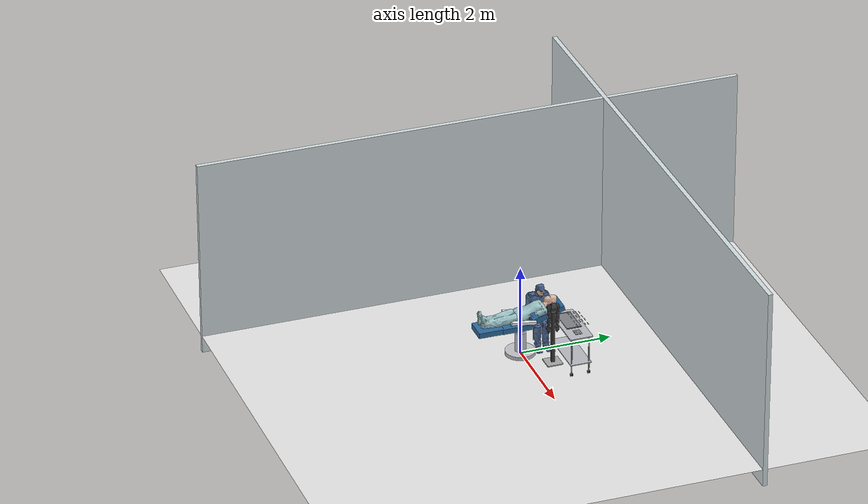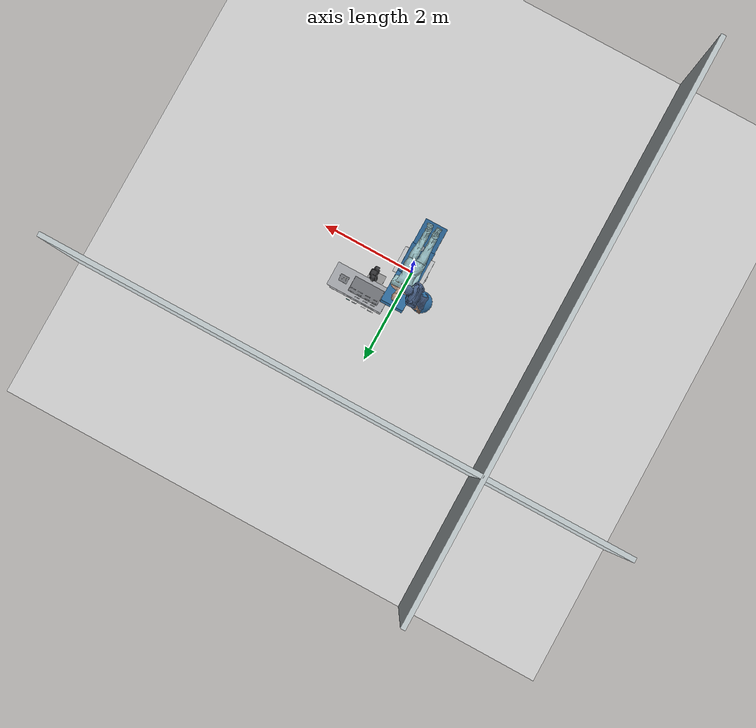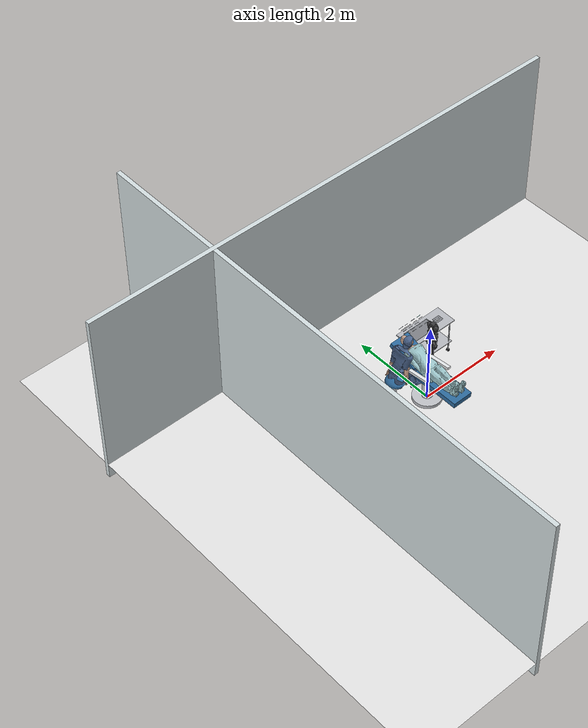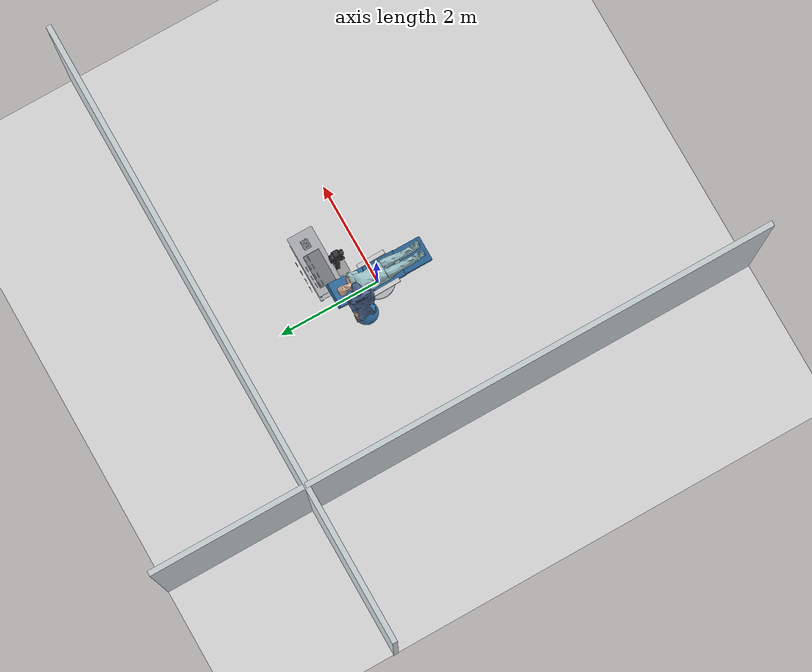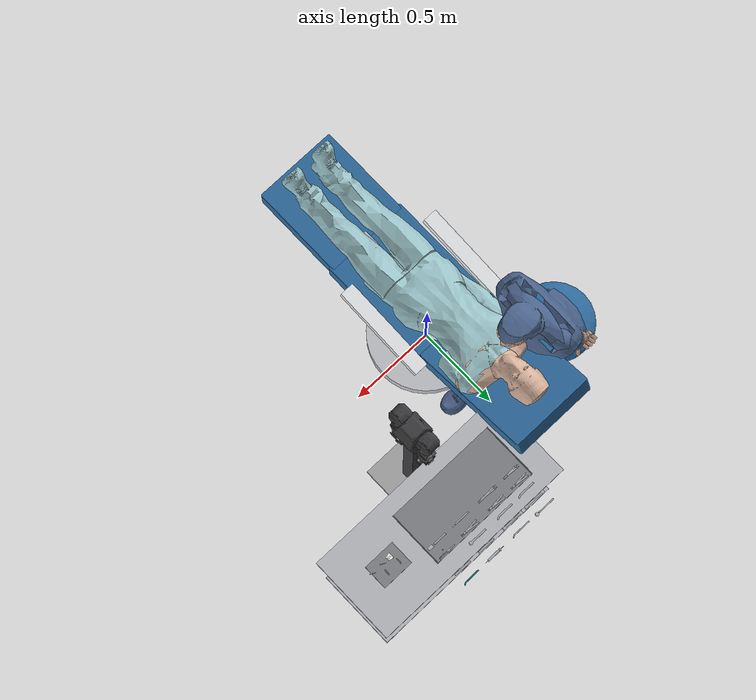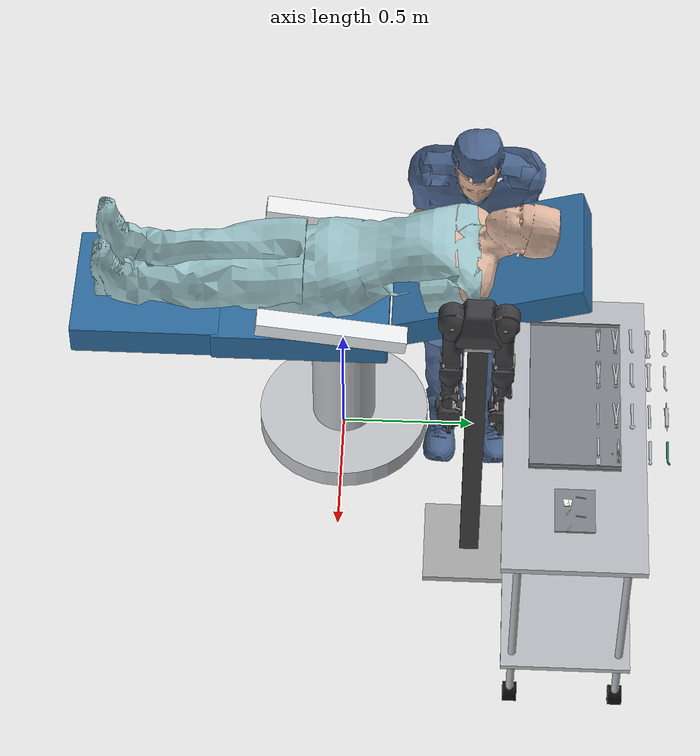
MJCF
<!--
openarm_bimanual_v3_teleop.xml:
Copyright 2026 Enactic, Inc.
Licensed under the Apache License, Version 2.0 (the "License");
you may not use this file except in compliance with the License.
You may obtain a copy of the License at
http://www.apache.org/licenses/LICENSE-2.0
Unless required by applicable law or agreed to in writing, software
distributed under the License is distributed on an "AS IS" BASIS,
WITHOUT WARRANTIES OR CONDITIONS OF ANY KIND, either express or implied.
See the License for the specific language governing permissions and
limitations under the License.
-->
<mujoco model="dental_demo_v3_blender">
  <include file="openarm_bimanual_v3_teleop.xml"/>
  <include file="room_v3_teleop.xml"/>

  <!-- 물리 안정화: Euler 통합기는 기구처럼 관성이 1e-7 수준인 물체의 접촉에서 발산한다.
       implicitfast 는 감쇠/접촉을 암시적으로 처리해 같은 timestep 에서 훨씬 안정적. -->
  <option integrator="implicitfast"/>

  <visual>
    <global offwidth="1280" offheight="720"/>
    <headlight active="1" ambient="0.42 0.42 0.45" diffuse="0.55 0.55 0.58" specular="0.25 0.25 0.28"/>
    <quality shadowsize="8192" offsamples="8"/>
    <map shadowclip="2.5" shadowscale="0.7" znear="0.02"/>
    <rgba haze="0.16 0.18 0.22 1"/>
  </visual>

  <worldbody>
    <light name="key"  pos="0.3 -0.8 2.2" dir="0 0.3 -1" diffuse="0.8 0.8 0.8"/>
    <light name="fill" pos="-0.5 0.6 2.0" dir="0.2 -0.2 -1" diffuse="0.45 0.45 0.5"/>
    <light name="rim" pos="1.4 0.8 1.9" dir="-0.5 -0.3 -1" diffuse="0.35 0.34 0.32" specular="0.4 0.4 0.4"/>
    <geom name="floor" type="plane" size="6 6 0.1" rgba="0.9 0.9 0.9 1"/>
    <geom name="wall_back" type="box" pos="0 3 1.8" size="6 0.05 2.2" rgba="0.83 0.87 0.88 1"/>
    <geom name="wall_side" type="box" pos="-3 0 1.8" size="0.05 6 2.2" rgba="0.83 0.87 0.88 1"/>
    <camera name="wide" pos="2.05 -2.15 2.05" fovy="46" mode="targetbody" target="cam_target"/>
    <!-- 스테이징 구도용: 의사(-0.88,0.58) - 환자 - 로봇(0.79,0.50) 3자가 한 프레임에 -->
    <camera name="staging" pos="-0.95 -2.10 1.75" fovy="40" mode="targetbody" target="cam_target"/>
  </worldbody>
  <!-- home: 텔레옵 시작 자세 = 양 전완을 앞으로 굽힌 준비자세
       (팔을 내리면 트레이 상면 z=0.924 에 걸린다. 앞으로 굽히면 팔 최저 z=1.077 로 여유)
       원래 주석: 텔레옵 시작 자세. 로봇 팔 어깨 벌림 + 의사 오른팔을 전달구역으로 내민 자세 -->
  <keyframe>
    <key name="home" qpos="0.01195 -0.47994 -0.03509 1.50437 -1.33829 0.03254 -0.37899 0.00000 0.00000 0.00059 0.39362 0.01363 1.76267 -1.13880 -0.32493 0.28859 0.00000 0.00000 1.81917 0.08000 0.00150 0.70711 0.00000 0.00000 0.70711 1.55972 0.08000 0.00150 0.70711 0.00000 0.00000 0.70711 1.59636 -0.07368 0.00150 0.70510 0.00000 0.00000 0.70911 1.62361 0.26000 0.00150 0.70711 0.00000 0.00000 0.70711 -0.45166 1.14740 -0.01585 -0.68769 0.00000 0.00000 0.72600 -0.41435 1.29521 -0.00276 -0.68769 0.00000 0.00000 0.72600 1.65411 0.40999 0.00073 0.70711 0.00000 0.00000 0.70711 -0.31962 1.08263 0.00168 -0.70711 0.00000 0.00000 0.70711 -0.28831 1.24058 -0.00108 -0.70711 0.00000 0.00000 0.70711 -0.25625 1.42056 -0.00108 0.70711 0.00000 0.00000 -0.70711 -0.88000 1.08000 0.00150 -0.70711 0.00000 0.00000 0.70711 -0.09887 1.08030 0.00030 -0.70711 0.00000 0.00000 0.70711 -0.82454 1.29117 0.00321 -0.69137 0.00000 0.00000 0.72250 -0.51222 1.58000 0.00150 -0.70711 0.00000 0.00000 0.70711 -0.48350 1.64399 -0.00104 -0.68698 0.00000 0.00000 0.72668 -0.54417 1.42000 0.00150 -0.70711 0.00000 0.00000 0.70711 -0.06642 1.24022 0.00023 -0.70711 0.00000 0.00000 0.70711 1.97111 0.08000 0.00150 0.70711 0.00000 0.00000 0.70711 1.38311 -0.03144 0.00060 0.69001 0.00000 0.00000 0.72380 0.76030 3.00000 0.97483 0.03472 1.19992" ctrl="0.01195 -0.47994 -0.03509 1.50437 -1.33829 0.03254 -0.37899 0.00000 0.00059 0.39362 0.01363 1.76267 -1.13880 -0.32493 0.28859 0.00000"/>
    <!-- handoff: 로봇 왼팔이 전달지점까지 IK 로 뻗은 자세 (도달 검증용) -->
    <key name="handoff" qpos="-1.55805 0.02167 -0.61542 0.08538 -1.12500 -0.15599 0.97583 0.00000 0.00000 0.00059 0.39362 0.01363 1.76267 -1.13880 -0.32493 0.28859 0.00000 0.00000 1.81917 0.08000 0.00150 0.70711 0.00000 0.00000 0.70711 1.55972 0.08000 0.00150 0.70711 0.00000 0.00000 0.70711 1.59636 -0.07368 0.00150 0.70510 0.00000 0.00000 0.70911 1.62361 0.26000 0.00150 0.70711 0.00000 0.00000 0.70711 -0.45166 1.14740 -0.01585 -0.68769 0.00000 0.00000 0.72600 -0.41435 1.29521 -0.00276 -0.68769 0.00000 0.00000 0.72600 1.65411 0.40999 0.00073 0.70711 0.00000 0.00000 0.70711 -0.31962 1.08263 0.00168 -0.70711 0.00000 0.00000 0.70711 -0.28831 1.24058 -0.00108 -0.70711 0.00000 0.00000 0.70711 -0.25625 1.42056 -0.00108 0.70711 0.00000 0.00000 -0.70711 -0.88000 1.08000 0.00150 -0.70711 0.00000 0.00000 0.70711 -0.09887 1.08030 0.00030 -0.70711 0.00000 0.00000 0.70711 -0.82454 1.29117 0.00321 -0.69137 0.00000 0.00000 0.72250 -0.51222 1.58000 0.00150 -0.70711 0.00000 0.00000 0.70711 -0.48350 1.64399 -0.00104 -0.68698 0.00000 0.00000 0.72668 -0.54417 1.42000 0.00150 -0.70711 0.00000 0.00000 0.70711 -0.06642 1.24022 0.00023 -0.70711 0.00000 0.00000 0.70711 1.97111 0.08000 0.00150 0.70711 0.00000 0.00000 0.70711 1.38311 -0.03144 0.00060 0.69001 0.00000 0.00000 0.72380 0.76030 3.00000 0.97483 0.03472 1.19992" ctrl="-1.55805 0.02167 -0.61542 0.08538 -1.12500 -0.15599 0.97583 0.00000 0.00059 0.39362 0.01363 1.76267 -1.13880 -0.32493 0.28859 0.00000"/>
  </keyframe>
</mujoco>

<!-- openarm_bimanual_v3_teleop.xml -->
<mujoco model="openarm_v20">
  <default>
    <joint stiffness="0" ref="0.0" />
    <default class="robot">
      <default class="motor_DM8009">
        <joint frictionloss="0.2" damping="1.0" armature="0.0081" limited="true" type="hinge" />
        <motor forcelimited="true" forcerange="-40 40" />
      </default>
      <default class="motor_DM4340">
        <joint frictionloss="0.1" damping="0.9" armature="0.1600" limited="true" type="hinge" />
        <motor forcelimited="true" forcerange="-27 27" />
      </default>
      <default class="motor_DM4310">
        <joint frictionloss="0.04" damping="0.9" armature="0.0100" limited="true" type="hinge" />
        <motor forcelimited="true" forcerange="-7 7" />
      </default>
      <default class="motor_DM3507">
        <joint frictionloss="0.01" damping="0.01" armature="0.0049" limited="true" type="hinge" />
        <motor forcelimited="true" forcerange="-7 7" />
      </default>
      <default class="motor_finger">
        <joint limited="true" type="hinge" damping="2" />
        <position forcelimited="true" forcerange="-333 333" ctrllimited="true" ctrlrange="0 0.7854" />
      </default>
      <default class="lifter">
        <joint limited="true" type="slide" damping="50" />
        <position forcelimited="true" forcerange="-3000 3000" ctrllimited="true" ctrlrange="0 0.3" />
      </default>
      <default class="position_DM8009">
        <position kp="200" kv="150" forcelimited="true" forcerange="-40 40" />
      </default>
      <default class="position_DM4340">
        <position kp="100" kv="30" forcelimited="true" forcerange="-27 27" />
      </default>
      <default class="position_DM4310">
        <position kp="200" kv="5" forcelimited="true" forcerange="-7 7" />
      </default>
      <default class="position_DM3507">
        <position kp="200" kv="5" forcelimited="true" forcerange="-7 7" />
      </default>
      <default class="position_lifter">
        <position kp="8000" kv="4000" forcelimited="true" forcerange="-3000 3000" />
      </default>
      <default class="collision">
        <geom material="collision_material" condim="3" conaffinity="1" priority="1" group="3" solref="0.005 1" friction="1 0.01 0.01" />
        <equality solimp="0.99 0.999 1e-05" solref="0.005 1" />
      </default>
      <default class="visual">
        <geom material="visualgeom" contype="0" conaffinity="0" group="2" />
      </default>
    </default>
  </default>
  <compiler angle="radian" meshdir="assets" />
  <asset>
    <material name="collision_material" rgba="0.8 0.2 0.2 0.5" />
    <material name="visualgeom" rgba="0.7 0.7 0.7 1" />
    <material name="pale_silver" rgba="0.752941 0.752941 0.752941 1" specular="1.0" shininess="0.9" reflectance="0.8" />
    <material name="metal_silver" rgba="0.65 0.65 0.65 1.0" specular="1.0" shininess="0.9" reflectance="0.8" />
    <material name="matte_black" rgba="0.235 0.235 0.245 1.0" reflectance="0.15" shininess="0.35" specular="0.4" />
    <mesh name="body_link0_v" content_type="model/obj" file="visual/body/body_link0_5.obj" scale="0.001 0.001 0.001" />

    <mesh name="base_link_left_00" content_type="model/obj" file="visual/arm/base_link_00.obj" scale="1 -1 1" />
    <mesh name="base_link_left_01" content_type="model/obj" file="visual/arm/base_link_01.obj" scale="1 -1 1" />
    <mesh name="base_link_left_collision_00" content_type="model/stl" file="collision/base_link.stl" scale="1 -1 1" />
    <mesh name="link1_left_00" content_type="model/obj" file="visual/arm/link1_00.obj" scale="1 -1 1" />
    <mesh name="link1_left_01" content_type="model/obj" file="visual/arm/link1_01.obj" scale="1 -1 1" />
    <mesh name="link1_left_02" content_type="model/obj" file="visual/arm/link1_02.obj" scale="1 -1 1" />
    <mesh name="link1_left_collision_00" content_type="model/stl" file="collision/link1.stl" scale="1 -1 1" />
    <mesh name="link2_left_00" content_type="model/obj" file="visual/arm/link2_00.obj" scale="1 -1 1" />
    <mesh name="link2_left_01" content_type="model/obj" file="visual/arm/link2_01.obj" scale="1 -1 1" />
    <mesh name="link2_left_02" content_type="model/obj" file="visual/arm/link2_02.obj" scale="1 -1 1" />
    <mesh name="link2_left_collision_00" content_type="model/stl" file="collision/link2.stl" scale="1 -1 1" />
    <mesh name="link3_left_00" content_type="model/obj" file="visual/arm/link3_00.obj" />
    <mesh name="link3_left_01" content_type="model/obj" file="visual/arm/link3_01.obj" />
    <mesh name="link3_left_02" content_type="model/obj" file="visual/arm/link3_02.obj" />
    <mesh name="link3_left_collision_00" content_type="model/stl" file="collision/link3.stl" />
    <mesh name="link4_left_00" content_type="model/obj" file="visual/arm/link4_00.obj" />
    <mesh name="link4_left_01" content_type="model/obj" file="visual/arm/link4_01.obj" />
    <mesh name="link4_left_02" content_type="model/obj" file="visual/arm/link4_02.obj" />
    <mesh name="link4_left_collision_00" content_type="model/stl" file="collision/link4.stl" />
    <mesh name="link5_left_00" content_type="model/obj" file="visual/arm/link5_00.obj" scale="1 -1 1" />
    <mesh name="link5_left_01" content_type="model/obj" file="visual/arm/link5_01.obj" scale="1 -1 1" />
    <mesh name="link5_left_02" content_type="model/obj" file="visual/arm/link5_02.obj" scale="1 -1 1" />
    <mesh name="link5_left_collision_00" content_type="model/stl" file="collision/link5_part_00.stl" scale="1 -1 1" />
    <mesh name="link5_left_collision_01" content_type="model/stl" file="collision/link5_part_01.stl" scale="1 -1 1" />
    <mesh name="link5_left_collision_02" content_type="model/stl" file="collision/link5_part_02.stl" scale="1 -1 1" />
    <mesh name="link6_left_00" content_type="model/obj" file="visual/arm/link6_00.obj" scale="1 -1 1" />
    <mesh name="link6_left_01" content_type="model/obj" file="visual/arm/link6_01.obj" scale="1 -1 1" />
    <mesh name="link6_left_02" content_type="model/obj" file="visual/arm/link6_02.obj" scale="1 -1 1" />
    <mesh name="link6_left_collision_00" content_type="model/stl" file="collision/link6.stl" scale="1 -1 1" />
    <mesh name="ee_base_link_left_00" content_type="model/obj" file="visual/gripper/ee_base_link_00.obj" scale="1 -1 1" />
    <mesh name="ee_base_link_left_01" content_type="model/obj" file="visual/gripper/ee_base_link_01.obj" scale="1 -1 1" />
    <mesh name="ee_base_link_left_02" content_type="model/obj" file="visual/gripper/ee_base_link_02.obj" scale="1 -1 1" />
    <mesh name="ee_base_link_left_collision_00" content_type="model/stl" file="collision/ee_base_link.stl" scale="1 -1 1" />
    <mesh name="finger_inner_left_00" content_type="model/obj" file="visual/gripper/finger_inner_00.obj" scale="1 -1 1" />
    <mesh name="finger_inner_left_01" content_type="model/obj" file="visual/gripper/finger_inner_01.obj" scale="1 -1 1" />
    <mesh name="finger_inner_left_02" content_type="model/obj" file="visual/gripper/finger_inner_02.obj" scale="1 -1 1" />
    <mesh name="finger_inner_left_collision_00" content_type="model/stl" file="collision/finger_inner_part_00.stl" scale="1 -1 1" />
    <mesh name="finger_inner_left_collision_01" content_type="model/stl" file="collision/finger_inner_part_01.stl" scale="1 -1 1" />
    <mesh name="finger_inner_left_collision_02" content_type="model/stl" file="collision/finger_inner_part_02.stl" scale="1 -1 1" />
    <mesh name="finger_inner_left_collision_03" content_type="model/stl" file="collision/finger_inner_part_03.stl" scale="1 -1 1" />
    <mesh name="finger_outer_left_00" content_type="model/obj" file="visual/gripper/finger_outer_00.obj" scale="1 -1 1" />
    <mesh name="finger_outer_left_01" content_type="model/obj" file="visual/gripper/finger_outer_01.obj" scale="1 -1 1" />
    <mesh name="finger_outer_left_02" content_type="model/obj" file="visual/gripper/finger_outer_02.obj" scale="1 -1 1" />
    <mesh name="finger_outer_left_collision_00" content_type="model/stl" file="collision/finger_outer_part_00.stl" scale="1 -1 1" />
    <mesh name="finger_outer_left_collision_01" content_type="model/stl" file="collision/finger_outer_part_01.stl" scale="1 -1 1" />
    <mesh name="finger_outer_left_collision_02" content_type="model/stl" file="collision/finger_outer_part_02.stl" scale="1 -1 1" />
    <mesh name="finger_outer_left_collision_03" content_type="model/stl" file="collision/finger_outer_part_03.stl" scale="1 -1 1" />
    <mesh name="base_link_right_00" content_type="model/obj" file="visual/arm/base_link_00.obj" />
    <mesh name="base_link_right_01" content_type="model/obj" file="visual/arm/base_link_01.obj" />
    <mesh name="base_link_right_collision_00" content_type="model/stl" file="collision/base_link.stl" />
    <mesh name="link1_right_00" content_type="model/obj" file="visual/arm/link1_00.obj" />
    <mesh name="link1_right_01" content_type="model/obj" file="visual/arm/link1_01.obj" />
    <mesh name="link1_right_02" content_type="model/obj" file="visual/arm/link1_02.obj" />
    <mesh name="link1_right_collision_00" content_type="model/stl" file="collision/link1.stl" />
    <mesh name="link2_right_00" content_type="model/obj" file="visual/arm/link2_00.obj" />
    <mesh name="link2_right_01" content_type="model/obj" file="visual/arm/link2_01.obj" />
    <mesh name="link2_right_02" content_type="model/obj" file="visual/arm/link2_02.obj" />
    <mesh name="link2_right_collision_00" content_type="model/stl" file="collision/link2.stl" />
    <mesh name="link3_right_00" content_type="model/obj" file="visual/arm/link3_00.obj" />
    <mesh name="link3_right_01" content_type="model/obj" file="visual/arm/link3_01.obj" />
    <mesh name="link3_right_02" content_type="model/obj" file="visual/arm/link3_02.obj" />
    <mesh name="link3_right_collision_00" content_type="model/stl" file="collision/link3.stl" />
    <mesh name="link4_right_00" content_type="model/obj" file="visual/arm/link4_00.obj" />
    <mesh name="link4_right_01" content_type="model/obj" file="visual/arm/link4_01.obj" />
    <mesh name="link4_right_02" content_type="model/obj" file="visual/arm/link4_02.obj" />
    <mesh name="link4_right_collision_00" content_type="model/stl" file="collision/link4.stl" />
    <mesh name="link5_right_00" content_type="model/obj" file="visual/arm/link5_00.obj" />
    <mesh name="link5_right_01" content_type="model/obj" file="visual/arm/link5_01.obj" />
    <mesh name="link5_right_02" content_type="model/obj" file="visual/arm/link5_02.obj" />
    <mesh name="link5_right_collision_00" content_type="model/stl" file="collision/link5_part_00.stl" />
    <mesh name="link5_right_collision_01" content_type="model/stl" file="collision/link5_part_01.stl" />
    <mesh name="link5_right_collision_02" content_type="model/stl" file="collision/link5_part_02.stl" />
    <mesh name="link6_right_00" content_type="model/obj" file="visual/arm/link6_00.obj" />
    <mesh name="link6_right_01" content_type="model/obj" file="visual/arm/link6_01.obj" />
    <mesh name="link6_right_02" content_type="model/obj" file="visual/arm/link6_02.obj" />
    <mesh name="link6_right_collision_00" content_type="model/stl" file="collision/link6.stl" />
    <mesh name="ee_base_link_right_00" content_type="model/obj" file="visual/gripper/ee_base_link_00.obj" />
    <mesh name="ee_base_link_right_01" content_type="model/obj" file="visual/gripper/ee_base_link_01.obj" />
    <mesh name="ee_base_link_right_02" content_type="model/obj" file="visual/gripper/ee_base_link_02.obj" />
    <mesh name="ee_base_link_right_collision_00" content_type="model/stl" file="collision/ee_base_link.stl" />
    <mesh name="finger_inner_right_00" content_type="model/obj" file="visual/gripper/finger_inner_00.obj" />
    <mesh name="finger_inner_right_01" content_type="model/obj" file="visual/gripper/finger_inner_01.obj" />
    <mesh name="finger_inner_right_02" content_type="model/obj" file="visual/gripper/finger_inner_02.obj" />
    <mesh name="finger_inner_right_collision_00" content_type="model/stl" file="collision/finger_inner_part_00.stl" />
    <mesh name="finger_inner_right_collision_01" content_type="model/stl" file="collision/finger_inner_part_01.stl" />
    <mesh name="finger_inner_right_collision_02" content_type="model/stl" file="collision/finger_inner_part_02.stl" />
    <mesh name="finger_inner_right_collision_03" content_type="model/stl" file="collision/finger_inner_part_03.stl" />
    <mesh name="finger_outer_right_00" content_type="model/obj" file="visual/gripper/finger_outer_00.obj" />
    <mesh name="finger_outer_right_01" content_type="model/obj" file="visual/gripper/finger_outer_01.obj" />
    <mesh name="finger_outer_right_02" content_type="model/obj" file="visual/gripper/finger_outer_02.obj" />
    <mesh name="finger_outer_right_collision_00" content_type="model/stl" file="collision/finger_outer_part_00.stl" />
    <mesh name="finger_outer_right_collision_01" content_type="model/stl" file="collision/finger_outer_part_01.stl" />
    <mesh name="finger_outer_right_collision_02" content_type="model/stl" file="collision/finger_outer_part_02.stl" />
    <mesh name="finger_outer_right_collision_03" content_type="model/stl" file="collision/finger_outer_part_03.stl" />
  </asset>
  <worldbody>
    <!-- arm origin site: pose origin for FK/IK, placed at the model root so it
         lands on the attach frame wherever the bimanual arms are mounted
         (group 4 = hidden by default) -->
    <site name="arm_origin" pos="0.58 0.5 1.32" size="0.02" rgba="1 0.8 0 1" group="4"/>
    <body name="openarm_torso" pos="0.58 0.5 0.622" quat="0 0 0 1">
      <geom name="openarm_torso_visual" type="mesh" mesh="body_link0_v" class="visual" material="matte_black"/>
      <!-- 지지대: 기존 0.10x0.14 각기둥은 팔(어깨폭 0.062)에 비해 과하게 굵었다.
           실제 암 스탠드에 맞춰 지름 0.09 원형 포스트 + 지름 0.40 원판 베이스로 축소.
           (양팔 총 질량 ~10kg 을 1.2m 높이에서 받치는 데 필요한 최소 수준) -->
      <!-- 지지대: 사각 기둥 + 사각 받침대 (실사용 형상). 기존 0.10x0.14 는 팔에 비해 굵어
           0.07x0.07 각기둥 + 0.34x0.34 각판으로 축소. -->
      <geom name="oa_ped_column" type="box" pos="0 0 -0.004" size="0.035 0.035 0.617" class="visual" material="matte_black"/>
      <geom name="oa_ped_collar" type="box" pos="0 0 0.600" size="0.048 0.048 0.018" class="visual" material="metal_silver"/>
      <geom name="oa_ped_foot"   type="box" pos="0 0 -0.612" size="0.170 0.170 0.012" class="visual" material="metal_silver"/>
      <!-- 충돌체: 위 3개는 class="visual"(contype=0) 이라 팔이 기둥을 그대로 관통했다.
           박스로 근사한 충돌 geom 을 따로 넣어 팔이 기둥·받침대·몸통에 부딪히게 한다.
           group="3" 이라 뷰어 기본 화면에는 안 보이고 물리에만 관여. -->
      <geom name="oa_ped_column_col" type="box" pos="0 0 -0.004" size="0.035 0.035 0.617" class="collision" priority="3" solref="0.001 1" solimp="0.995 0.9995 0.0005" condim="3"/>
      <geom name="oa_ped_collar_col" type="box" pos="0 0 0.600" size="0.048 0.048 0.018" class="collision" priority="3" solref="0.001 1" solimp="0.995 0.9995 0.0005" condim="3"/>
      <geom name="oa_ped_foot_col"   type="box" pos="0 0 -0.612" size="0.170 0.170 0.012" class="collision" priority="3" solref="0.001 1" solimp="0.995 0.9995 0.0005" condim="3"/>
      <geom name="openarm_torso_col" type="box" pos="-0.014 0 0.692" size="0.080 0.077 0.089" class="collision" priority="3" solref="0.001 1" solimp="0.995 0.9995 0.0005" condim="3"/>
    </body>
    <body name="openarm_left_base_link" pos="0.58 0.531 1.32" quat="0 0 0 1">
      <inertial pos="-0.00253124 0.0258186 -2.70658e-05" quat="-1.46856942085e-06 0.70739772103 0.706815721259 2.1457591538e-05" mass="1.14323" diaginertia="0.00159935 0.00113608 0.000750542" />
      <geom name="base_link_left_00" type="mesh" mesh="base_link_left_00" class="visual" material="matte_black" quat="0 0 1 0" />
      <geom name="base_link_left_01" type="mesh" mesh="base_link_left_01" class="visual" material="pale_silver" quat="0 0 1 0" />
      <geom name="base_link_left_collision_00" type="mesh" mesh="base_link_left_collision_00" class="collision" quat="0 0 1 0" />
      <body name="openarm_left_link1" pos="0 0.0625 0">
        <inertial pos="0.00090035 0.044466 2.88441e-05" quat="0.999901 -0.000371041 -5.04627e-05 -0.0140338" mass="1.14167" diaginertia="0.00109459 0.000758935 0.000670659" />
        <joint name="openarm_left_joint1" pos="0 0 0" axis="0 1 0" range="-3.4907 1.3963" actuatorfrcrange="-40 40" class="motor_DM8009" />
        <geom name="link1_left_00" type="mesh" mesh="link1_left_00" class="visual" material="matte_black" />
        <geom name="link1_left_01" type="mesh" mesh="link1_left_01" class="visual" material="pale_silver" />
        <geom name="link1_left_02" type="mesh" mesh="link1_left_02" class="visual" material="metal_silver" />
        <geom name="link1_left_collision_00" type="mesh" mesh="link1_left_collision_00" class="collision" />
        <body name="openarm_left_link2" pos="0 0.06 0">
          <inertial pos="-0.0247185 -7.60578e-08 -0.0312643" quat="0.999342 -6.47495e-06 -0.0362804 3.02331e-06" mass="0.277509" diaginertia="0.000153968 0.000113062 8.19211e-05" />
          <joint name="openarm_left_joint2" pos="0 0 0" axis="-1 0 0" range="-3.3161 0.17453" actuatorfrcrange="-40 40" class="motor_DM8009" />
          <geom name="link2_left_00" type="mesh" mesh="link2_left_00" class="visual" material="matte_black" />
          <geom name="link2_left_01" type="mesh" mesh="link2_left_01" class="visual" material="metal_silver" />
          <geom name="link2_left_02" type="mesh" mesh="link2_left_02" class="visual" material="pale_silver" />
          <geom name="link2_left_collision_00" type="mesh" mesh="link2_left_collision_00" class="collision" />
          <body name="openarm_left_link3" pos="0 0 -0.06625">
            <inertial pos="-0.00300862 -0.000514813 -0.109368" quat="0.998906 -0.00891348 0.0458105 0.00280505" mass="1.07386" diaginertia="0.00129561 0.00114038 0.000553361" />
            <joint name="openarm_left_joint3" pos="0 0 0" axis="0 0 -1" range="-1.5708 1.5708" actuatorfrcrange="-27 27" class="motor_DM4340" />
            <geom name="link3_left_00" type="mesh" mesh="link3_left_00" class="visual" material="matte_black" />
            <geom name="link3_left_01" type="mesh" mesh="link3_left_01" class="visual" material="metal_silver" />
            <geom name="link3_left_02" type="mesh" mesh="link3_left_02" class="visual" material="pale_silver" />
            <geom name="link3_left_collision_00" type="mesh" mesh="link3_left_collision_00" class="collision" />
            <body name="openarm_left_link4" pos="0 0 -0.15375">
              <inertial pos="-0.00310326 -0.00136539 -0.0574601" quat="0.996952 0.00947325 0.00348083 0.0773554" mass="0.634853" diaginertia="0.000469894 0.000433114 0.000245134" />
              <joint name="openarm_left_joint4" pos="0 0 0" axis="0 -1 0" range="0 2.4435" actuatorfrcrange="-27 27" class="motor_DM4340" />
              <geom name="link4_left_00" type="mesh" mesh="link4_left_00" class="visual" material="matte_black" />
              <geom name="link4_left_01" type="mesh" mesh="link4_left_01" class="visual" material="pale_silver" />
              <geom name="link4_left_02" type="mesh" mesh="link4_left_02" class="visual" material="metal_silver" />
              <geom name="link4_left_collision_00" type="mesh" mesh="link4_left_collision_00" class="collision" />
              <body name="openarm_left_link5" pos="0 0 -0.0955">
                <inertial pos="-0.000737189 0.000412407 -0.0470938" quat="0.685547 -0.0023482 -0.00297125 0.728019" mass="0.615659" diaginertia="0.000334799 0.00027946 0.000176657" />
                <joint name="openarm_left_joint5" pos="0 0 0" axis="0 0 -1" range="-1.5708 1.5708" actuatorfrcrange="-7 7" class="motor_DM4310" />
                <geom name="link5_left_00" type="mesh" mesh="link5_left_00" class="visual" material="matte_black" />
                <geom name="link5_left_01" type="mesh" mesh="link5_left_01" class="visual" material="pale_silver" />
                <geom name="link5_left_02" type="mesh" mesh="link5_left_02" class="visual" material="metal_silver" />
                <geom name="link5_left_collision_00" type="mesh" mesh="link5_left_collision_00" class="collision" />
                <geom name="link5_left_collision_01" type="mesh" mesh="link5_left_collision_01" class="collision" />
                <geom name="link5_left_collision_02" type="mesh" mesh="link5_left_collision_02" class="collision" />
                <body name="openarm_left_link6" pos="0 0 -0.1205">
                  <inertial pos="2.27438e-05 -0.000686496 5.44e-05" quat="0.999832 -0.0183155 0.000397003 -0.000757974" mass="0.475203" diaginertia="0.000179276 0.000136249 0.000135339" />
                  <joint name="openarm_left_joint6" pos="0 0 0" axis="0 -1 0" range="-0.7854 0.7854" actuatorfrcrange="-7 7" class="motor_DM4310" />
                  <geom name="link6_left_00" type="mesh" mesh="link6_left_00" class="visual" material="matte_black" />
                  <geom name="link6_left_01" type="mesh" mesh="link6_left_01" class="visual" material="metal_silver" />
                  <geom name="link6_left_02" type="mesh" mesh="link6_left_02" class="visual" material="pale_silver" />
                  <geom name="link6_left_collision_00" type="mesh" mesh="link6_left_collision_00" class="collision" />
                  <body name="openarm_left_ee_base_link">
                    <inertial pos="0.0137902 -0.0084073 -0.05938" quat="0.760121 0.648846 -0.0304587 -0.0169317" mass="0.52832" diaginertia="0.000219417 0.000166122 0.000155742" />
                    <joint name="openarm_left_joint7" pos="0 0 0" axis="1 0 0" range="-1.5708 1.5708" actuatorfrcrange="-7 7" class="motor_DM3507" />
                    <geom name="ee_base_link_left_00" pos="0.0205 0 0" quat="1 0 0 0" type="mesh" mesh="ee_base_link_left_00" class="visual" material="matte_black" />
                    <geom name="ee_base_link_left_01" pos="0.0205 0 0" type="mesh" mesh="ee_base_link_left_01" class="visual" material="metal_silver" />
                    <geom name="ee_base_link_left_02" pos="0.0205 0 0" type="mesh" mesh="ee_base_link_left_02" class="visual" material="pale_silver" />
                    <geom name="ee_base_link_left_collision_00" pos="0.0205 0 0" quat="1 0 0 0" type="mesh" mesh="ee_base_link_left_collision_00" class="collision" />
                    <camera name="camera_wrist_left" pos="0.023 0.0182 -0.10236" euler="-0.366519 0.22689 -1.5708" fovy="66" resolution="960 600"/>
                    <site name="left_ee_control_point" pos="0 0 0.0" size="0.01" rgba="0 1 0 1" />
                    <site name="left_gripper_tip" pos="-0.0219 0 -0.0686" size="0.008" rgba="1 1 0 1" />
                    <body name="openarm_left_ee_inner_finger" pos="-0.00143 -0.018 -0.068">
                      <inertial pos="-0.0124991 -0.00176593 -0.0241663" quat="0.982638 0.0922084 -0.15927 -0.0235197" mass="0.125979" diaginertia="3.8543e-05 3.6883e-05 1.43942e-05" />
                      <joint name="openarm_left_finger_joint1" pos="0 0 0" axis="-1 0 0" range="0 0.7854" actuatorfrcrange="-10 10" class="motor_finger" />
                      <geom name="finger_inner_left_00" type="mesh" mesh="finger_inner_left_00" class="visual" material="matte_black" />
                      <geom name="finger_inner_left_01" type="mesh" mesh="finger_inner_left_01" class="visual" material="matte_black" />
                      <geom name="finger_inner_left_02" type="mesh" mesh="finger_inner_left_02" class="visual" material="pale_silver" />
                      <geom name="finger_inner_left_collision_00" type="mesh" mesh="finger_inner_left_collision_00" class="collision" />
                      <geom name="finger_inner_left_collision_01" type="mesh" mesh="finger_inner_left_collision_01" class="collision" />
                      <geom name="finger_inner_left_collision_02" type="mesh" mesh="finger_inner_left_collision_02" class="collision" />
                      <geom name="finger_inner_left_collision_03" type="mesh" mesh="finger_inner_left_collision_03" class="collision" />
                    </body>
                    <body name="openarm_left_ee_outer_finger" pos="-0.00143 0.018 -0.068">
                      <inertial pos="-0.012796 0.0020183 -0.026792" quat="0.982097 -0.0906989 -0.165079 0.00294117" mass="0.11372" diaginertia="3.70662e-05 3.60159e-05 1.33599e-05" />
                      <joint name="openarm_left_finger_joint2" pos="0 0 0" axis="1 0 0" range="0 0.7854" actuatorfrcrange="-10 10" class="motor_finger" />
                      <geom name="finger_outer_left_00" type="mesh" mesh="finger_outer_left_00" class="visual" material="matte_black" />
                      <geom name="finger_outer_left_01" type="mesh" mesh="finger_outer_left_01" class="visual" material="matte_black" />
                      <geom name="finger_outer_left_02" type="mesh" mesh="finger_outer_left_02" class="visual" material="pale_silver" />
                      <geom name="finger_outer_left_collision_00" type="mesh" mesh="finger_outer_left_collision_00" class="collision" />
                      <geom name="finger_outer_left_collision_01" type="mesh" mesh="finger_outer_left_collision_01" class="collision" />
                      <geom name="finger_outer_left_collision_02" type="mesh" mesh="finger_outer_left_collision_02" class="collision" />
                      <geom name="finger_outer_left_collision_03" type="mesh" mesh="finger_outer_left_collision_03" class="collision" />
                    </body>
                  </body>
                </body>
              </body>
            </body>
          </body>
        </body>
      </body>
    </body>
    <body name="openarm_right_base_link" pos="0.58 0.469 1.32" quat="0 0 0 1">
      <inertial pos="-0.00253124 -0.0258186 -2.70658e-05" quat="2.1457591538e-05 0.706815721259 0.70739772103 -1.46856942085e-06" mass="1.14323" diaginertia="0.00159935 0.00113608 0.000750542" />
      <geom name="base_link_right_00" type="mesh" mesh="base_link_right_00" class="visual" material="matte_black" quat="0 0 1 0" />
      <geom name="base_link_right_01" type="mesh" mesh="base_link_right_01" class="visual" material="pale_silver" quat="0 0 1 0" />
      <geom name="base_link_right_collision_00" type="mesh" mesh="base_link_right_collision_00" class="collision" quat="0 0 1 0" />
      <body name="openarm_right_link1" pos="0 -0.0625 0">
        <inertial pos="0.00090035 -0.044466 2.88441e-05" quat="0.999901 0.000371041 -5.04627e-05 0.0140338" mass="1.14167" diaginertia="0.00109459 0.000758935 0.000670659" />
        <joint name="openarm_right_joint1" pos="0 0 0" axis="0 -1 0" range="-1.3963 3.4907" actuatorfrcrange="-40 40" class="motor_DM8009" />
        <geom name="link1_right_00" type="mesh" mesh="link1_right_00" class="visual" material="matte_black" />
        <geom name="link1_right_01" type="mesh" mesh="link1_right_01" class="visual" material="pale_silver" />
        <geom name="link1_right_02" type="mesh" mesh="link1_right_02" class="visual" material="metal_silver" />
        <geom name="link1_right_collision_00" type="mesh" mesh="link1_right_collision_00" class="collision" />
        <body name="openarm_right_link2" pos="0 -0.06 0">
          <inertial pos="-0.0247185 7.60578e-08 -0.0312643" quat="0.999342 6.47495e-06 -0.0362804 -3.02331e-06" mass="0.277509" diaginertia="0.000153968 0.000113062 8.19211e-05" />
          <joint name="openarm_right_joint2" pos="0 0 0" axis="-1 0 0" range="-0.17453 3.3161" actuatorfrcrange="-40 40" class="motor_DM8009" />
          <geom name="link2_right_00" type="mesh" mesh="link2_right_00" class="visual" material="matte_black" />
          <geom name="link2_right_01" type="mesh" mesh="link2_right_01" class="visual" material="metal_silver" />
          <geom name="link2_right_02" type="mesh" mesh="link2_right_02" class="visual" material="pale_silver" />
          <geom name="link2_right_collision_00" type="mesh" mesh="link2_right_collision_00" class="collision" />
          <body name="openarm_right_link3" pos="0 0 -0.06625">
            <inertial pos="-0.00300862 -0.000514813 -0.109368" quat="0.998906 -0.00891348 0.0458105 0.00280505" mass="1.07386" diaginertia="0.00129561 0.00114038 0.000553361" />
            <joint name="openarm_right_joint3" pos="0 0 0" axis="0 0 -1" range="-1.5708 1.5708" actuatorfrcrange="-27 27" class="motor_DM4340" />
            <geom name="link3_right_00" type="mesh" mesh="link3_right_00" class="visual" material="matte_black" />
            <geom name="link3_right_01" type="mesh" mesh="link3_right_01" class="visual" material="metal_silver" />
            <geom name="link3_right_02" type="mesh" mesh="link3_right_02" class="visual" material="pale_silver" />
            <geom name="link3_right_collision_00" type="mesh" mesh="link3_right_collision_00" class="collision" />
            <body name="openarm_right_link4" pos="0 0 -0.15375">
              <inertial pos="-0.00310326 -0.00136539 -0.0574601" quat="0.996952 0.00947325 0.00348083 0.0773554" mass="0.634853" diaginertia="0.000469894 0.000433114 0.000245134" />
              <joint name="openarm_right_joint4" pos="0 0 0" axis="0 -1 0" range="0 2.4435" actuatorfrcrange="-27 27" class="motor_DM4340" />
              <geom name="link4_right_00" type="mesh" mesh="link4_right_00" class="visual" material="matte_black" />
              <geom name="link4_right_01" type="mesh" mesh="link4_right_01" class="visual" material="pale_silver" />
              <geom name="link4_right_02" type="mesh" mesh="link4_right_02" class="visual" material="metal_silver" />
              <geom name="link4_right_collision_00" type="mesh" mesh="link4_right_collision_00" class="collision" />
              <body name="openarm_right_link5" pos="0 0 -0.0955">
                <inertial pos="-0.000737189 -0.000412407 -0.0470938" quat="0.728019 -0.00297125 -0.0023482 0.685547" mass="0.615659" diaginertia="0.000334799 0.00027946 0.000176657" />
                <joint name="openarm_right_joint5" pos="0 0 0" axis="0 0 -1" range="-1.5708 1.5708" actuatorfrcrange="-7 7" class="motor_DM4310" />
                <geom name="link5_right_00" type="mesh" mesh="link5_right_00" class="visual" material="matte_black" />
                <geom name="link5_right_01" type="mesh" mesh="link5_right_01" class="visual" material="pale_silver" />
                <geom name="link5_right_02" type="mesh" mesh="link5_right_02" class="visual" material="metal_silver" />
                <geom name="link5_right_collision_00" type="mesh" mesh="link5_right_collision_00" class="collision" />
                <geom name="link5_right_collision_01" type="mesh" mesh="link5_right_collision_01" class="collision" />
                <geom name="link5_right_collision_02" type="mesh" mesh="link5_right_collision_02" class="collision" />
                <body name="openarm_right_link6" pos="0 0 -0.1205">
                  <inertial pos="2.27438e-05 0.000686496 5.44e-05" quat="0.999832 0.0183155 0.000397003 0.000757974" mass="0.475203" diaginertia="0.000179276 0.000136249 0.000135339" />
                  <joint name="openarm_right_joint6" pos="0 0 0" axis="0 1 0" range="-0.7854 0.7854" actuatorfrcrange="-7 7" class="motor_DM4310" />
                  <geom name="link6_right_00" type="mesh" mesh="link6_right_00" class="visual" material="matte_black" />
                  <geom name="link6_right_01" type="mesh" mesh="link6_right_01" class="visual" material="metal_silver" />
                  <geom name="link6_right_02" type="mesh" mesh="link6_right_02" class="visual" material="pale_silver" />
                  <geom name="link6_right_collision_00" type="mesh" mesh="link6_right_collision_00" class="collision" />
                  <body name="openarm_right_ee_base_link">
                    <inertial pos="0.0137902 0.0084073 -0.05938" quat="0.648846 0.760121 0.0169317 0.0304587" mass="0.52832" diaginertia="0.000219417 0.000166122 0.000155742" />
                    <joint name="openarm_right_joint7" pos="0 0 0" axis="1 0 0" range="-1.5708 1.5708" actuatorfrcrange="-7 7" class="motor_DM3507" />
                    <geom name="ee_base_link_right_00" pos="0.0205 0 0" quat="1 0 0 0" type="mesh" mesh="ee_base_link_right_00" class="visual" material="matte_black" />
                    <geom name="ee_base_link_right_01" pos="0.0205 0 0" type="mesh" mesh="ee_base_link_right_01" class="visual" material="metal_silver" />
                    <geom name="ee_base_link_right_02" pos="0.0205 0 0" type="mesh" mesh="ee_base_link_right_02" class="visual" material="pale_silver" />
                    <geom name="ee_base_link_right_collision_00" pos="0.0205 0 0" quat="1 0 0 0" type="mesh" mesh="ee_base_link_right_collision_00" class="collision" />
                    <camera name="camera_wrist_right" pos="0.023 -0.0182 -0.10236" euler="0.366519 0.22689 -1.5708" fovy="66" resolution="960 600"/>
                    <site name="right_ee_control_point" pos="0.0 0.0 0.0" size="0.01" rgba="1 0 0 1" />
                    <site name="right_gripper_tip" pos="-0.0219 0 -0.0686" size="0.008" rgba="1 1 0 1" />
                    <body name="openarm_right_ee_inner_finger" pos="-0.00143 0.018 -0.068">
                      <inertial pos="-0.0124991 0.00176593 -0.0241663" quat="0.982638 -0.0922084 -0.15927 0.0235197" mass="0.125979" diaginertia="3.8543e-05 3.6883e-05 1.43942e-05" />
                      <joint name="openarm_right_finger_joint1" pos="0 0 0" axis="-1 0 0" range="-0.7854 0" actuatorfrcrange="-10 10" class="motor_finger" />
                      <geom name="finger_inner_right_00" type="mesh" mesh="finger_inner_right_00" class="visual" material="matte_black" />
                      <geom name="finger_inner_right_01" type="mesh" mesh="finger_inner_right_01" class="visual" material="matte_black" />
                      <geom name="finger_inner_right_02" type="mesh" mesh="finger_inner_right_02" class="visual" material="pale_silver" />
                      <geom name="finger_inner_right_collision_00" type="mesh" mesh="finger_inner_right_collision_00" class="collision" />
                      <geom name="finger_inner_right_collision_01" type="mesh" mesh="finger_inner_right_collision_01" class="collision" />
                      <geom name="finger_inner_right_collision_02" type="mesh" mesh="finger_inner_right_collision_02" class="collision" />
                      <geom name="finger_inner_right_collision_03" type="mesh" mesh="finger_inner_right_collision_03" class="collision" />
                    </body>
                    <body name="openarm_right_ee_outer_finger" pos="-0.00143 -0.018 -0.068">
                      <inertial pos="-0.012796 -0.0020183 -0.026792" quat="0.982097 0.0906989 -0.165079 -0.00294117" mass="0.11372" diaginertia="3.70662e-05 3.60159e-05 1.33599e-05" />
                      <joint name="openarm_right_finger_joint2" pos="0 0 0" axis="1 0 0" range="-0.7854 0" actuatorfrcrange="-10 10" class="motor_finger" />
                      <geom name="finger_outer_right_00" type="mesh" mesh="finger_outer_right_00" class="visual" material="matte_black" />
                      <geom name="finger_outer_right_01" type="mesh" mesh="finger_outer_right_01" class="visual" material="matte_black" />
                      <geom name="finger_outer_right_02" type="mesh" mesh="finger_outer_right_02" class="visual" material="pale_silver" />
                      <geom name="finger_outer_right_collision_00" type="mesh" mesh="finger_outer_right_collision_00" class="collision" />
                      <geom name="finger_outer_right_collision_01" type="mesh" mesh="finger_outer_right_collision_01" class="collision" />
                      <geom name="finger_outer_right_collision_02" type="mesh" mesh="finger_outer_right_collision_02" class="collision" />
                      <geom name="finger_outer_right_collision_03" type="mesh" mesh="finger_outer_right_collision_03" class="collision" />
                    </body>
                  </body>
                </body>
              </body>
            </body>
          </body>
        </body>
      </body>
    </body>
  </worldbody>
  <equality>
    <joint name="openarm_left_ee_finger_joint_mimic" joint1="openarm_left_finger_joint1" joint2="openarm_left_finger_joint2" polycoef="0 1 0 0 0" solimp="0.95 0.99 0.001" solref="0.005 1" />
    <joint name="openarm_right_ee_finger_joint_mimic" joint1="openarm_right_finger_joint1" joint2="openarm_right_finger_joint2" polycoef="0 1 0 0 0" solimp="0.95 0.99 0.001" solref="0.005 1" />
  </equality>
  <actuator>
    <position name="left_joint1_ctrl" joint="openarm_left_joint1" class="position_DM8009" kp="230" kv="2.7" ctrllimited="true" ctrlrange="-3.49066 1.39626" />
    <position name="left_joint2_ctrl" joint="openarm_left_joint2" class="position_DM8009" kp="230" kv="2.7" ctrllimited="true" ctrlrange="-3.31613 0.174533" />
    <position name="left_joint3_ctrl" joint="openarm_left_joint3" class="position_DM4340" kp="190" kv="2.2" ctrllimited="true" ctrlrange="-1.5708 1.5708" />
    <position name="left_joint4_ctrl" joint="openarm_left_joint4" class="position_DM4340" kp="190" kv="2.2" ctrllimited="true" ctrlrange="0 2.44346" />
    <position name="left_joint5_ctrl" joint="openarm_left_joint5" class="position_DM4310" kp="30" kv="1.5" ctrllimited="true" ctrlrange="-1.5708 1.5708" />
    <position name="left_joint6_ctrl" joint="openarm_left_joint6" class="position_DM4310" kp="30" kv="1.5" ctrllimited="true" ctrlrange="-0.785398 0.785398" />
    <position name="left_joint7_ctrl" joint="openarm_left_joint7" class="position_DM4310" kp="30" kv="1.5" ctrllimited="true" ctrlrange="-1.5708 1.5708" />
    <position name="left_finger1_ctrl" joint="openarm_left_finger_joint1" class="position_DM4310" kp="30" kv="0.2" ctrllimited="true" ctrlrange="0 0.7854" />
    <position name="right_joint1_ctrl" joint="openarm_right_joint1" class="position_DM8009" kp="230" kv="2.7" ctrllimited="true" ctrlrange="-1.39626 3.49066" />
    <position name="right_joint2_ctrl" joint="openarm_right_joint2" class="position_DM8009" kp="230" kv="2.7" ctrllimited="true" ctrlrange="-0.174533 3.31613" />
    <position name="right_joint3_ctrl" joint="openarm_right_joint3" class="position_DM4340" kp="190" kv="2.2" ctrllimited="true" ctrlrange="-1.5708 1.5708" />
    <position name="right_joint4_ctrl" joint="openarm_right_joint4" class="position_DM4340" kp="190" kv="2.2" ctrllimited="true" ctrlrange="0 2.44346" />
    <position name="right_joint5_ctrl" joint="openarm_right_joint5" class="position_DM4310" kp="30" kv="1.5" ctrllimited="true" ctrlrange="-1.5708 1.5708" />
    <position name="right_joint6_ctrl" joint="openarm_right_joint6" class="position_DM4310" kp="30" kv="1.5" ctrllimited="true" ctrlrange="-0.785398 0.785398" />
    <position name="right_joint7_ctrl" joint="openarm_right_joint7" class="position_DM4310" kp="30" kv="1.5" ctrllimited="true" ctrlrange="-1.5708 1.5708" />
    <position name="right_finger1_ctrl" joint="openarm_right_finger_joint1" class="position_DM4310" kp="30" kv="0.2" ctrllimited="true" ctrlrange="-0.7854 0" />
  </actuator>
  <contact>

  </contact>
  <!-- torso 하우징 안을 어깨 링크가 지나가는 것은 실제 구조상 정상이므로 해당 쌍만 충돌 제외.
       (기둥·받침대와의 충돌은 그대로 살아 있어 팔이 기둥을 관통하지 않는다) -->
  <contact>
    <exclude body1="openarm_torso" body2="openarm_left_base_link"/>
    <exclude body1="openarm_torso" body2="openarm_left_link1"/>
    <exclude body1="openarm_torso" body2="openarm_left_link2"/>
    <exclude body1="openarm_torso" body2="openarm_right_base_link"/>
    <exclude body1="openarm_torso" body2="openarm_right_link1"/>
    <exclude body1="openarm_torso" body2="openarm_right_link2"/>
  </contact>
</mujoco>

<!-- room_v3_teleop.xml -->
<mujoco model="dental_room">

    <asset>
    <!-- DocCap_* = 원본 리그의 열린 절단면(팔꿈치·손목·어깨)을 막은 사본.
         teleop/tools/cap_doctor_holes.py 로 생성. 원본 DocPart_* 는 그대로 둔다. -->
    <mesh name="doc_torso" file="doctor_rig/DocPart_torso.obj"/>
    <mesh name="doc_upper_arm" file="doctor_rig/DocPart_upper_arm.obj"/>
    <mesh name="doc_forearm" file="doctor_rig/DocCap_forearm.obj"/>
    <mesh name="doc_hand" file="doctor_rig/DocCap_hand.obj"/>
    <mesh name="doc_head" file="doctor_rig/DocPart2_head.obj"/>
    <mesh name="doc_cap_mask" file="doctor_rig/DocPart3_cap_mask.obj"/>
    <mesh name="doc_face_skin" file="doctor_rig/DocCap_faceskin.obj"/>
    <mesh name="doc_left_hand" file="doctor_rig/DocCap_left_hand.obj"/>
    <mesh name="doc_torso_only" file="doctor_rig/DocPart2_torso_only.obj"/>
    <!-- 스테이징: 서 있는 몸통 메시를 골반(z=0.90)/무릎(z=0.52)에서 절단한 앉은자세용 3분할 -->
    <mesh name="doc_seat_torso" file="doctor_rig/DocSeat_torso.obj"/>
    <mesh name="doc_seat_thigh" file="doctor_rig/DocSeat_thigh.obj"/>
    <mesh name="doc_seat_shin"  file="doctor_rig/DocSeat_shin.obj"/>
    <mesh name="doc_seat_lhand" file="doctor_rig/DocSeat_lhand.obj"/>
    <!-- 환자: 의사와 같은 인체 메시(DocPart_torso = 머리·양팔 포함 전신)를 0.96배(신장 1.746 m)로
         줄여 가랑이 z=0.768 / 목 z=1.440 에서 3분할. 앙와위 강체변환은 아래 patient body 참조. -->
    <mesh name="pat_head"  file="doctor_rig/PatSupine_head.obj"/>
    <mesh name="pat_torso" file="doctor_rig/PatSupine_torso.obj"/>
    <mesh name="pat_legs"  file="doctor_rig/PatSupine_legs.obj"/>
    <material name="doc_scrub" rgba="0.30 0.40 0.56 1"/>
    <material name="doc_skin" rgba="0.85 0.68 0.58 1"/>
    <material name="patient_gown" rgba="0.62 0.78 0.80 1" shininess="0.25" specular="0.15"/>
    <material name="patient_skin" rgba="0.87 0.72 0.63 1" shininess="0.3" specular="0.2"/>
      <material name="bl_Chrome" rgba="0.75 0.76 0.78 1.0" shininess="0.85" specular="0.8" reflectance="0.65"/>
    <material name="bl_CushionBlue" rgba="0.18 0.42 0.62 1.0" shininess="0.45" specular="0.2" reflectance="0.15"/>
    <material name="bl_WhitePlastic" rgba="0.92 0.93 0.94 1.0" shininess="0.7" specular="0.2" reflectance="0.15"/>
    <material name="bl_DarkPlastic" rgba="0.06 0.06 0.07 1.0" shininess="0.65" specular="0.2" reflectance="0.15"/>
    <material name="bl_CartFrame" rgba="0.72 0.73 0.75 1.0" shininess="0.65" specular="0.74" reflectance="0.6"/>
    <material name="bl_SurgSteel" rgba="0.68 0.7 0.72 1.0" shininess="0.68" specular="0.71" reflectance="0.57"/>
    <material name="bl_RootPickerPlastic" rgba="0.1 0.45 0.42 1.0" shininess="0.6" specular="0.2" reflectance="0.15"/>
    <material name="bl_TraySteel" rgba="0.5 0.51 0.53 1.0" shininess="0.6" specular="0.62" reflectance="0.5"/>
    <material name="bl_PackagingWhite" rgba="0.95 0.96 0.92 1.0" shininess="0.55" specular="0.2" reflectance="0.15"/>
    <!-- 실물 규격 보정: 베이스 지름 0.90 -> 0.65 m (실물 0.55~0.70), 기둥 0.12 m 단축 -->
    <mesh name="bl_Chair_Base" file="blender_scene/Chair_Base.obj" scale="0.722 0.722 1"/>
    <mesh name="bl_Chair_Column" file="blender_scene/Chair_Column.obj" scale="1 1 0.782"/>
    <mesh name="bl_Chair_Column_Upper" file="blender_scene/Chair_Column_Upper.obj"/>
    <mesh name="bl_Seat_Pan" file="blender_scene/Seat_Pan.obj"/>
    <mesh name="bl_Leg_Rest" file="blender_scene/Leg_Rest.obj"/>
    <mesh name="bl_Backrest" file="blender_scene/Backrest.obj"/>
    <mesh name="bl_Headrest" file="blender_scene/Headrest.obj"/>
    <mesh name="bl_Armrest_L" file="blender_scene/Armrest_L.obj"/>
    <mesh name="bl_Armrest_R" file="blender_scene/Armrest_R.obj"/>
    <mesh name="bl_Cart_Caster_-1_-1" file="blender_scene/Cart_Caster_-1_-1.obj"/>
    <mesh name="bl_Cart_Caster_-1_1" file="blender_scene/Cart_Caster_-1_1.obj"/>
    <mesh name="bl_Cart_Caster_1_-1" file="blender_scene/Cart_Caster_1_-1.obj"/>
    <mesh name="bl_Cart_Caster_1_1" file="blender_scene/Cart_Caster_1_1.obj"/>
    <mesh name="bl_Cart_Post_-1_-1" file="blender_scene/Cart_Post_-1_-1.obj"/>
    <mesh name="bl_Cart_Post_-1_1" file="blender_scene/Cart_Post_-1_1.obj"/>
    <mesh name="bl_Cart_Post_1_-1" file="blender_scene/Cart_Post_1_-1.obj"/>
    <mesh name="bl_Cart_Post_1_1" file="blender_scene/Cart_Post_1_1.obj"/>
    <mesh name="bl_Cart_Shelf_Bottom" file="blender_scene/Cart_Shelf_Bottom.obj"/>
    <mesh name="bl_Cart_Shelf_Top" file="blender_scene/Cart_Shelf_Top.obj"/>
    <mesh name="bl_Curette_Lucas85" file="blender_scene/Curette_Lucas85.obj"/>
    <mesh name="bl_Elevator_301" file="blender_scene/Elevator_301.obj"/>
    <mesh name="bl_Elevator_34S" file="blender_scene/Elevator_34S.obj"/>
    <mesh name="bl_Elevator_Buser" file="blender_scene/Elevator_Buser.obj"/>
    <mesh name="bl_Elevator_Cryer73" file="blender_scene/Elevator_Cryer73.obj"/>
    <mesh name="bl_Elevator_Cryer74" file="blender_scene/Elevator_Cryer74.obj"/>
    <mesh name="bl_Elevator_Molt" file="blender_scene/Elevator_Molt.obj"/>
    <mesh name="bl_Forceps_FX150" file="blender_scene/Forceps_FX150.obj"/>
    <mesh name="bl_Forceps_FX151" file="blender_scene/Forceps_FX151.obj"/>
    <mesh name="bl_Forceps_FX17" file="blender_scene/Forceps_FX17.obj"/>
    <mesh name="bl_Mirror" file="blender_scene/Mirror.obj"/>
    <mesh name="bl_NeedleHolder" file="blender_scene/NeedleHolder.obj"/>
    <mesh name="bl_Probe" file="blender_scene/Probe.obj"/>
    <mesh name="bl_Retractor_Minnesota" file="blender_scene/Retractor_Minnesota.obj"/>
    <mesh name="bl_RootPicker" file="blender_scene/RootPicker.obj"/>
    <mesh name="bl_Scalpel_No3" file="blender_scene/Scalpel_No3.obj"/>
    <mesh name="bl_SuctionRack_Base" file="blender_scene/SuctionRack_Base.obj"/>
    <mesh name="bl_SuctionTip_SUS_a" file="blender_scene/SuctionTip_SUS_a.obj"/>
    <mesh name="bl_SuctionTip_SUS_b" file="blender_scene/SuctionTip_SUS_b.obj"/>
    <mesh name="bl_SuctionTip_Ti_a" file="blender_scene/SuctionTip_Ti_a.obj"/>
    <mesh name="bl_SuctionTip_Ti_b" file="blender_scene/SuctionTip_Ti_b.obj"/>
    <mesh name="bl_Suture_Packet" file="blender_scene/Suture_Packet.obj"/>
    <mesh name="bl_Suture_Packet_2" file="blender_scene/Suture_Packet_2.obj"/>
    <mesh name="bl_SutureScissors_Dean" file="blender_scene/SutureScissors_Dean.obj"/>
    <mesh name="bl_Syringe_Aspirating" file="blender_scene/Syringe_Aspirating.obj"/>
    <mesh name="bl_TissueForceps_Adson" file="blender_scene/TissueForceps_Adson.obj"/>
    <mesh name="bl_Tray_Base" file="blender_scene/Tray_Base.obj"/>
    <mesh name="bl_Tray_RowDivider_0" file="blender_scene/Tray_RowDivider_0.obj"/>
    <mesh name="bl_Tray_RowDivider_1" file="blender_scene/Tray_RowDivider_1.obj"/>
    <mesh name="bl_Tray_RowDivider_2" file="blender_scene/Tray_RowDivider_2.obj"/>
    <mesh name="bl_Tray_RowDivider_3" file="blender_scene/Tray_RowDivider_3.obj"/>
    <mesh name="bl_Tray_RowDivider_4" file="blender_scene/Tray_RowDivider_4.obj"/>
    <mesh name="bl_Tray_SideWall_-0.32" file="blender_scene/Tray_SideWall_-0.32.obj"/>
    <mesh name="bl_Tray_SideWall_0.32" file="blender_scene/Tray_SideWall_0.32.obj"/>
    <mesh name="bl_Stool_Base" file="blender_scene/Stool_Base.obj"/>
    <mesh name="bl_Stool_Pole" file="blender_scene/Stool_Pole.obj"/>
    <mesh name="bl_Stool_Seat" file="blender_scene/Stool_Seat.obj"/>
</asset>

  <worldbody>
    <!-- ============ 치과의자 세트 (Blender 원본 그대로: 형태·색·재질) ============ -->
    <body name="bl_chair" pos="0 0 0">
      <geom name="bl_Chair_Base_g" type="mesh" mesh="bl_Chair_Base" material="bl_Chrome"/>
      <geom name="bl_Chair_Column_g" type="mesh" mesh="bl_Chair_Column" material="bl_Chrome" pos="0 0 0.0174"/>
      <!-- 기둥 위 전체를 0.12 m 내려 시트 상단 0.90 -> 0.78 (승강식 실물 범위 0.35~0.80) -->
      <body name="bl_chair_upper" pos="0 0 -0.12">
      <geom name="bl_Chair_Column_Upper_g" type="mesh" mesh="bl_Chair_Column_Upper" material="bl_Chrome"/>
      <geom name="bl_Seat_Pan_g" type="mesh" mesh="bl_Seat_Pan" material="bl_CushionBlue"/>
      <!-- 리클라인: 등받이+헤드레스트를 등받이 하단 힌지 (0, 0.230, 0.878) 둘레로 -44° 회전.
           수직대비 28°(업라이트) -> 72°(앙와위). 메시는 월드좌표로 baked 되어 있으므로
           자식 body를 힌지 위치에 두고 geom을 -힌지만큼 되밀어 "힌지 둘레 회전"을 만든다. -->
      <body name="bl_chair_backrest" pos="0 0.230 0.8778" euler="-0.76794 0 0">
        <geom name="bl_Backrest_g" type="mesh" mesh="bl_Backrest" material="bl_CushionBlue" pos="0 -0.230 -0.8778"/>
        <!-- 헤드레스트는 등받이 레일을 따라 슬라이드하는 부품. 의자 전장(2.11 m)이 환자(1.75 m)보다
             길어 기본 위치에서는 머리가 안 닿으므로, 등받이 면을 따라 -0.367 m 내려 뒤통수를 받친다. -->
        <geom name="bl_Headrest_g" type="mesh" mesh="bl_Headrest" material="bl_CushionBlue" pos="0 -0.4024 -1.2021"/>
      </body>
      <!-- 레그레스트: 발쪽으로 7.9° 들려 있고 시트면보다 78mm 낮던 것을 수평 + 시트면(z=0.90) 정렬 -->
      <body name="bl_chair_legrest" pos="0 -0.454 0.900" euler="0.13746 0 0">
        <geom name="bl_Leg_Rest_g" type="mesh" mesh="bl_Leg_Rest" material="bl_CushionBlue" pos="0 0.454 -0.822"/>
      </body>
      <geom name="bl_Armrest_L_g" type="mesh" mesh="bl_Armrest_L" material="bl_WhitePlastic"/>
      <geom name="bl_Armrest_R_g" type="mesh" mesh="bl_Armrest_R" material="bl_WhitePlastic"/>
      </body>
      <site name="handoff" pos="0.050 0.470 1.200" size="0.018" rgba="0.2 0.9 0.4 0.55" group="3"/>
    </body>
    <body name="bl_cart" pos="0.0000 -0.2000 0.0000">
      <geom name="bl_Cart_Caster_-1_-1_g" type="mesh" mesh="bl_Cart_Caster_-1_-1" material="bl_DarkPlastic"/>
      <geom name="bl_Cart_Caster_-1_1_g" type="mesh" mesh="bl_Cart_Caster_-1_1" material="bl_DarkPlastic"/>
      <geom name="bl_Cart_Caster_1_-1_g" type="mesh" mesh="bl_Cart_Caster_1_-1" material="bl_DarkPlastic"/>
      <geom name="bl_Cart_Caster_1_1_g" type="mesh" mesh="bl_Cart_Caster_1_1" material="bl_DarkPlastic"/>
      <geom name="bl_Cart_Post_-1_-1_g" type="mesh" mesh="bl_Cart_Post_-1_-1" material="bl_CartFrame"/>
      <geom name="bl_Cart_Post_-1_1_g" type="mesh" mesh="bl_Cart_Post_-1_1" material="bl_CartFrame"/>
      <geom name="bl_Cart_Post_1_-1_g" type="mesh" mesh="bl_Cart_Post_1_-1" material="bl_CartFrame"/>
      <geom name="bl_Cart_Post_1_1_g" type="mesh" mesh="bl_Cart_Post_1_1" material="bl_CartFrame"/>
      <geom name="bl_Cart_Shelf_Bottom_g" type="mesh" mesh="bl_Cart_Shelf_Bottom" material="bl_CartFrame"/>
      <geom name="bl_Cart_Shelf_Top_g" type="mesh" mesh="bl_Cart_Shelf_Top" material="bl_CartFrame"/>
    </body>
    <body name="bl_tray" pos="0.0000 -0.2000 0.0000">
      <geom name="bl_Tray_Base_g" type="mesh" mesh="bl_Tray_Base" material="bl_TraySteel"/>
      <geom name="bl_Tray_SideWall_-0.32_g" type="mesh" mesh="bl_Tray_SideWall_-0.32" material="bl_TraySteel"/>
      <geom name="bl_Tray_SideWall_0.32_g" type="mesh" mesh="bl_Tray_SideWall_0.32" material="bl_TraySteel"/>
    </body>
    <body name="bl_rack" pos="0.0000 -0.2000 0.0000">
      <geom name="bl_SuctionRack_Base_g" type="mesh" mesh="bl_SuctionRack_Base" material="bl_TraySteel"/>
      <geom name="bl_SuctionTip_SUS_a_g" type="mesh" mesh="bl_SuctionTip_SUS_a" material="bl_SurgSteel" density="7800" condim="4" priority="2" friction="1.2 0.05 0.01" solref="0.005 1" solimp="0.98 0.999 0.001"/>
      <geom name="bl_SuctionTip_SUS_b_g" type="mesh" mesh="bl_SuctionTip_SUS_b" material="bl_SurgSteel" density="7800" condim="4" priority="2" friction="1.2 0.05 0.01" solref="0.005 1" solimp="0.98 0.999 0.001"/>
      <geom name="bl_SuctionTip_Ti_a_g" type="mesh" mesh="bl_SuctionTip_Ti_a" material="bl_SurgSteel" density="7800" condim="4" priority="2" friction="1.2 0.05 0.01" solref="0.005 1" solimp="0.98 0.999 0.001"/>
      <geom name="bl_SuctionTip_Ti_b_g" type="mesh" mesh="bl_SuctionTip_Ti_b" material="bl_SurgSteel" density="7800" condim="4" priority="2" friction="1.2 0.05 0.01" solref="0.005 1" solimp="0.98 0.999 0.001"/>
      <geom name="bl_Suture_Packet_g" type="mesh" mesh="bl_Suture_Packet" material="bl_PackagingWhite" density="7800" condim="4" priority="2" friction="1.2 0.05 0.01" solref="0.005 1" solimp="0.98 0.999 0.001"/>
      <geom name="bl_Suture_Packet_2_g" type="mesh" mesh="bl_Suture_Packet_2" material="bl_PackagingWhite" density="7800" condim="4" priority="2" friction="1.2 0.05 0.01" solref="0.005 1" solimp="0.98 0.999 0.001"/>
    </body>
    <!-- 스테이징: 스툴을 환자 반대편(로봇 마주보는 자리)로 이동. 좌면중심 (-0.56, 0.48),
         좌면상단 z=0.588 -> 0.530 = 앉은 의사의 엉덩이 절단면(z=0.516)이 좌면에 묻히는 높이 -->
    <body name="bl_stool" pos="0.29 0.13 -0.058">
      <geom name="bl_Stool_Base_g" type="mesh" mesh="bl_Stool_Base" material="bl_DarkPlastic"/>
      <geom name="bl_Stool_Pole_g" type="mesh" mesh="bl_Stool_Pole" material="bl_Chrome"/>
      <geom name="bl_Stool_Seat_g" type="mesh" mesh="bl_Stool_Seat" material="bl_CushionBlue"/>
    </body>
    <!-- 기구 19종 — 전부 freejoint (자유 이동 물체). 이름/사이트 4개는 episode.py 호환용 유지 -->
    <body name="instr_curette_lucas85" pos="0 0 0">
      <joint type="free" armature="2e-5" damping="0.02"/>
      <geom name="bl_Curette_Lucas85_g" type="mesh" mesh="bl_Curette_Lucas85" material="bl_SurgSteel" density="7800" condim="4" priority="2" friction="1.2 0.05 0.01" solref="0.005 1" solimp="0.98 0.999 0.001"/>
    </body>
    <body name="instr_elevator" pos="0 0 0">
      <joint type="free" armature="2e-5" damping="0.02"/>
      <geom name="bl_Elevator_301_g" type="mesh" mesh="bl_Elevator_301" material="bl_SurgSteel" density="7800" condim="4" priority="2" friction="1.2 0.05 0.01" solref="0.005 1" solimp="0.98 0.999 0.001"/>
      <site name="elevator_R" pos="0.667 1.11 0.929" size="0.008" rgba="0.2 0.8 0.9 0.6" group="3"/>
    </body>
    <body name="instr_elevator_34s" pos="0 0 0">
      <joint type="free" armature="2e-5" damping="0.02"/>
      <geom name="bl_Elevator_34S_g" type="mesh" mesh="bl_Elevator_34S" material="bl_SurgSteel" density="7800" condim="4" priority="2" friction="1.2 0.05 0.01" solref="0.005 1" solimp="0.98 0.999 0.001"/>
    </body>
    <body name="instr_elevator_buser" pos="0 0 0">
      <joint type="free" armature="2e-5" damping="0.02"/>
      <geom name="bl_Elevator_Buser_g" type="mesh" mesh="bl_Elevator_Buser" material="bl_SurgSteel" density="7800" condim="4" priority="2" friction="1.2 0.05 0.01" solref="0.005 1" solimp="0.98 0.999 0.001"/>
    </body>
    <body name="instr_cryer" pos="0 0 0">
      <joint type="free" armature="2e-5" damping="0.02"/>
      <geom name="bl_Elevator_Cryer73_g" type="mesh" mesh="bl_Elevator_Cryer73" material="bl_SurgSteel" density="7800" condim="4" priority="2" friction="1.2 0.05 0.01" solref="0.005 1" solimp="0.98 0.999 0.001"/>
      <site name="cryer_R" pos="0.384 1.049 0.947" size="0.008" rgba="0.2 0.8 0.9 0.6" group="3"/>
    </body>
    <body name="instr_elevator_cryer74" pos="0 0 0">
      <joint type="free" armature="2e-5" damping="0.02"/>
      <geom name="bl_Elevator_Cryer74_g" type="mesh" mesh="bl_Elevator_Cryer74" material="bl_SurgSteel" density="7800" condim="4" priority="2" friction="1.2 0.05 0.01" solref="0.005 1" solimp="0.98 0.999 0.001"/>
    </body>
    <body name="instr_elevator_molt" pos="0 0 0">
      <joint type="free" armature="2e-5" damping="0.02"/>
      <geom name="bl_Elevator_Molt_g" type="mesh" mesh="bl_Elevator_Molt" material="bl_SurgSteel" density="7800" condim="4" priority="2" friction="1.2 0.05 0.01" solref="0.005 1" solimp="0.98 0.999 0.001"/>
    </body>
    <body name="instr_forceps150" pos="0 0 0">
      <joint type="free" armature="2e-5" damping="0.02"/>
      <geom name="bl_Forceps_FX150_g" type="mesh" mesh="bl_Forceps_FX150" material="bl_SurgSteel" density="7800" condim="4" priority="2" friction="1.2 0.05 0.01" solref="0.005 1" solimp="0.98 0.999 0.001"/>
      <site name="fx150_R" pos="0.364 0.992 0.931" size="0.008" rgba="0.2 0.8 0.9 0.6" group="3"/>
    </body>
    <body name="instr_forceps151" pos="0 0 0">
      <joint type="free" armature="2e-5" damping="0.02"/>
      <geom name="bl_Forceps_FX151_g" type="mesh" mesh="bl_Forceps_FX151" material="bl_SurgSteel" density="7800" condim="4" priority="2" friction="1.2 0.05 0.01" solref="0.005 1" solimp="0.98 0.999 0.001"/>
      <site name="fx151_R" pos="0.522 0.992 0.933" size="0.008" rgba="0.2 0.8 0.9 0.6" group="3"/>
    </body>
    <body name="instr_forceps_fx17" pos="0 0 0">
      <joint type="free" armature="2e-5" damping="0.02"/>
      <geom name="bl_Forceps_FX17_g" type="mesh" mesh="bl_Forceps_FX17" material="bl_SurgSteel" density="7800" condim="4" priority="2" friction="1.2 0.05 0.01" solref="0.005 1" solimp="0.98 0.999 0.001"/>
    </body>
    <body name="instr_mirror" pos="0 0 0">
      <joint type="free" armature="2e-5" damping="0.02"/>
      <geom name="bl_Mirror_g" type="mesh" mesh="bl_Mirror" material="bl_SurgSteel" density="7800" condim="4" priority="2" friction="1.2 0.05 0.01" solref="0.005 1" solimp="0.98 0.999 0.001"/>
    </body>
    <body name="instr_needleholder" pos="0 0 0">
      <joint type="free" armature="2e-5" damping="0.02"/>
      <geom name="bl_NeedleHolder_g" type="mesh" mesh="bl_NeedleHolder" material="bl_SurgSteel" density="7800" condim="4" priority="2" friction="1.2 0.05 0.01" solref="0.005 1" solimp="0.98 0.999 0.001"/>
    </body>
    <body name="instr_probe" pos="0 0 0">
      <joint type="free" armature="2e-5" damping="0.02"/>
      <geom name="bl_Probe_g" type="mesh" mesh="bl_Probe" material="bl_SurgSteel" density="7800" condim="4" priority="2" friction="1.2 0.05 0.01" solref="0.005 1" solimp="0.98 0.999 0.001"/>
    </body>
    <body name="instr_retractor_minnesota" pos="0 0 0">
      <joint type="free" armature="2e-5" damping="0.02"/>
      <geom name="bl_Retractor_Minnesota_g" type="mesh" mesh="bl_Retractor_Minnesota" material="bl_SurgSteel" density="7800" condim="4" priority="2" friction="1.2 0.05 0.01" solref="0.005 1" solimp="0.98 0.999 0.001"/>
    </body>
    <body name="instr_rootpicker" pos="0 0 0">
      <joint type="free" armature="2e-5" damping="0.02"/>
      <geom name="bl_RootPicker_g" type="mesh" mesh="bl_RootPicker" material="bl_RootPickerPlastic" density="7800" condim="4" priority="2" friction="1.2 0.05 0.01" solref="0.005 1" solimp="0.98 0.999 0.001"/>
    </body>
    <body name="instr_scalpel_no3" pos="0 0 0">
      <joint type="free" armature="2e-5" damping="0.02"/>
      <geom name="bl_Scalpel_No3_g" type="mesh" mesh="bl_Scalpel_No3" material="bl_SurgSteel" density="7800" condim="4" priority="2" friction="1.2 0.05 0.01" solref="0.005 1" solimp="0.98 0.999 0.001"/>
    </body>
    <body name="instr_suturescissors_dean" pos="0 0 0">
      <joint type="free" armature="2e-5" damping="0.02"/>
      <geom name="bl_SutureScissors_Dean_g" type="mesh" mesh="bl_SutureScissors_Dean" material="bl_SurgSteel" density="7800" condim="4" priority="2" friction="1.2 0.05 0.01" solref="0.005 1" solimp="0.98 0.999 0.001"/>
    </body>
    <body name="instr_syringe_aspirating" pos="0 0 0">
      <joint type="free" armature="2e-5" damping="0.02"/>
      <geom name="bl_Syringe_Aspirating_g" type="mesh" mesh="bl_Syringe_Aspirating" material="bl_SurgSteel" density="7800" condim="4" priority="2" friction="1.2 0.05 0.01" solref="0.005 1" solimp="0.98 0.999 0.001"/>
    </body>
    <body name="instr_tissueforceps_adson" pos="0 0 0">
      <joint type="free" armature="2e-5" damping="0.02"/>
      <geom name="bl_TissueForceps_Adson_g" type="mesh" mesh="bl_TissueForceps_Adson" material="bl_SurgSteel" density="7800" condim="4" priority="2" friction="1.2 0.05 0.01" solref="0.005 1" solimp="0.98 0.999 0.001"/>
    </body>

    <!-- ============ 로봇 받침대 (카트 옆, 트레이에 손이 닿는 위치) ============ -->

    <!-- ============ 의사 (Blender 리깅 캐릭터. 의자 헤드레스트 쪽 빈 공간으로 옮겨서
         로봇과 팔이 닿는 거리로 재배치 — 원래 의자 옆(y=0.35)은 의자 폭(0.9m)이 로봇과
         사이를 막아 팔이 안 닿았음. euler는 그대로 두고 위치만 옮김, 안 맞으면 조정 예정) -->
    <body name="patient" pos="0 0 0">
      <body name="patient_upper" pos="0 -0.8704 0.6554" quat="0.809017 -0.587785 0 0">
        <geom name="patient_torso_mesh" type="mesh" mesh="pat_torso" material="patient_gown"
              contype="0" conaffinity="0"/>
        <geom name="patient_head_mesh" type="mesh" mesh="pat_head" material="patient_skin"
              contype="0" conaffinity="0"/>
      </body>
      <!-- 충돌체: 시각 메시는 contype=0(물리 무영향)이라 로봇 그리퍼가 환자를 그대로 통과했다.
           메시-메시 충돌은 무겁고 불안정하므로 프리미티브로 몸을 근사해 충돌만 담당시킨다.
           group="3" 이라 뷰어 기본 화면에는 안 보인다. -->
      <geom name="pat_col_head"  type="sphere"  pos="0 0.655 1.135" size="0.105" group="3" rgba="1 0 0 0.25"/>
      <geom name="pat_col_chest" type="capsule" fromto="0 0.05 0.955 0 0.47 1.055" size="0.118" group="3" rgba="1 0 0 0.25"/>
      <geom name="pat_col_abdo"  type="capsule" fromto="0 -0.18 0.915 0 0.06 0.955" size="0.115" group="3" rgba="1 0 0 0.25"/>
      <geom name="pat_col_legs"  type="capsule" fromto="0 -0.18 0.900 0 -0.80 0.900" size="0.105" group="3" rgba="1 0 0 0.25"/>
      <geom name="pat_col_arm_l" type="capsule" fromto="-0.185 0.30 0.985 -0.195 -0.08 0.955" size="0.062" group="3" rgba="1 0 0 0.25"/>
      <geom name="pat_col_arm_r" type="capsule" fromto="0.185 0.30 0.985 0.195 -0.08 0.955" size="0.062" group="3" rgba="1 0 0 0.25"/>
      <body name="patient_lower" pos="0 -0.9059 0.9295" quat="0.707107 -0.707107 0 0">
        <geom name="patient_legs_mesh" type="mesh" mesh="pat_legs" material="patient_gown"
              contype="0" conaffinity="0"/>
      </body>
    </body>

    <body name="doctor_body" pos="-0.374 0.48 0" euler="0 0 1.5708">
      <!-- 상체 전방 경사 20°: 고관절 (0, 0.026, 0.636) 둘레 회전. 술자가 술야로 몸을 숙이는 자세이며,
           이게 있어야 어깨가 0.18 m 앞으로 나와 사양서 §9-2 전달구역 V 에 손이 닿는다.
           상체 조각이 이미 다리와 분리돼 있어 메시 재절단 없이 body 하나로 구현. -->
      <body name="doctor_upper" pos="0 0.026 0.636" euler="0.3491 0 0">
      <geom name="doctor_torso_mesh" type="mesh" mesh="doc_seat_torso" material="doc_scrub" pos="0 -0.026 -0.920" contype="0" conaffinity="0"/>
      <!-- 머리 속채움: cap_mask 는 두께 없는 껍데기라 각도에 따라 내부가 비쳐 "깨진" 것처럼 보인다.
           (메시 폭 0.40 m 는 수술모 끈까지 포함한 값이고, 끈은 얇은 리본이라 클로즈업에서 파편처럼 보인다)
           안쪽에 불투명 타원체를 넣어 관통 시야를 막는다. -->
      <geom name="doc_col_torso" type="capsule" fromto="0 -0.026 -0.30 0 -0.026 0.34" size="0.155" group="3" rgba="0 0 1 0.25"/>
      <geom name="doctor_head_core" type="ellipsoid" pos="0.002 0.019 0.723" size="0.076 0.086 0.106"
            material="doc_scrub"/>
      <geom name="doctor_capmask_mesh" type="mesh" mesh="doc_cap_mask" material="doc_scrub" pos="0 -0.026 -0.920" contype="0" conaffinity="0"/>
      <geom name="doctor_faceskin_mesh" type="mesh" mesh="doc_face_skin" material="doc_skin" pos="0 -0.026 -0.920" contype="0" conaffinity="0"/>
      <!-- 왼팔(팔뚝+손): 상체를 20° 숙이면 baked 된 팔이 함께 딸려와 "가슴에서 손이 나오는" 모양이 된다.
           실제로는 팔이 중력 방향으로 늘어지므로, 왼쪽 어깨 (-0.174, 0.060, 0.405) 둘레로
           상체 경사와 같은 크기만큼 반대로(-20°) 돌려 수직으로 되돌린다. -->
      <body name="doctor_l_arm" pos="-0.174 0.060 0.405" euler="-0.3491 0 0">
        <geom name="doctor_lefthand_mesh" type="mesh" mesh="doc_left_hand" material="doc_skin"
              pos="0.174 -0.086 -1.325" contype="0" conaffinity="0"/>
        <geom name="doctor_lhand_mesh" type="mesh" mesh="doc_seat_lhand" material="doc_skin"
              pos="0.174 -0.086 -1.325" contype="0" conaffinity="0"/>
      </body>
      <body name="doctor_r_shoulder" pos="0.174 0.060 0.405">
        <joint name="doctor_r_shoulder_yaw" armature="0.02"   type="hinge" axis="0 0 1" range="-1.3 1.3" limited="true" damping="3"/>
        <joint name="doctor_r_shoulder_pitch" armature="0.02" type="hinge" axis="1 0 0" range="-0.3 3.0" limited="true" damping="3"/>
        <joint name="doctor_r_shoulder_roll" armature="0.02"  type="hinge" axis="0 1 0" range="-1.3 1.3" limited="true" damping="3"/>
        <!-- 어깨 이음: 몸통 메시는 오른팔을 떼어낸 자리가 뚫려 V자 홈이 보인다.
             구멍을 메우면 면을 가로지르는 파편이 생기므로, 구 형태로 덮어 가린다. -->
        <geom name="doctor_shoulder_cap" type="ellipsoid" pos="-0.005 -0.008 0.100" size="0.058 0.056 0.052"
              material="doc_scrub"/>
        <geom name="doctor_upperarm_mesh" type="mesh" mesh="doc_upper_arm" material="doc_scrub" contype="0" conaffinity="0"/>
        <body name="doctor_r_elbow" pos="0.003 -0.006 -0.225">
          <joint name="doctor_r_elbow_joint" armature="0.02" type="hinge" axis="1 0 0" range="0 2.4" limited="true" damping="3"/>
          <geom name="doctor_forearm_mesh" type="mesh" mesh="doc_forearm" material="doc_skin" contype="0" conaffinity="0"/>
          <body name="doctor_r_wrist" pos="0.007 0.003 -0.180">
            <joint name="doctor_r_wrist_joint" armature="0.02" type="hinge" axis="1 0 0" range="-1.2 1.2" limited="true" damping="3"/>
            <geom name="doctor_palm" type="box" pos="0 0 -0.090" size="0.011 0.045 0.052"
                  material="doc_skin"/>
            <geom name="doctor_finger1" type="capsule" fromto="0.006 -0.033 -0.138 0.034 -0.034 -0.178" size="0.0095"
                  material="doc_skin"/>
            <geom name="doctor_finger2" type="capsule" fromto="0.006 -0.011 -0.140 0.037 -0.011 -0.184" size="0.0098"
                  material="doc_skin"/>
            <geom name="doctor_finger3" type="capsule" fromto="0.006 0.011 -0.140 0.036 0.011 -0.182" size="0.0096"
                  material="doc_skin"/>
            <geom name="doctor_finger4" type="capsule" fromto="0.006 0.032 -0.136 0.031 0.033 -0.172" size="0.0088"
                  material="doc_skin"/>
            <geom name="doctor_thumb" type="capsule" fromto="0.008 -0.046 -0.070 0.030 -0.080 -0.104" size="0.0110"
                  material="doc_skin"/>
            <geom name="doctor_wristpad" type="capsule" fromto="0 0 -0.030 0 0 -0.052" size="0.026"
                  material="doc_skin"/>
            <site name="doctor_r_grip" pos="-0.01 -0.02 -0.16" size="0.006" rgba="1 1 0 0.6" group="3"/>
          </body>
        </body>
      </body>
      </body>
      <!-- 다리는 상체 경사를 따라가면 안 되므로 doctor_upper 밖(= doctor_body 직속)에 둔다 -->
      <body name="doctor_thigh" pos="0 -0.8694 0.4229" quat="0.793353 -0.608761 0 0">
        <geom name="doctor_thigh_mesh" type="mesh" mesh="doc_seat_thigh" material="doc_scrub" contype="0" conaffinity="0"/>
      </body>
      <body name="doctor_shin" pos="0 -0.4151 0.0150">
        <geom name="doctor_shin_mesh" type="mesh" mesh="doc_seat_shin" material="doc_scrub" contype="0" conaffinity="0"/>
      </body>
    </body>

    <!-- ============ 수술준비대(카트) + 트레이 (Blender 실측: 카트 1.2x0.5m, 트레이 0.64x0.32m) ============ -->
    <!-- 로봇과 같은 편으로 옮김 + 2026-09-05 로봇이 뒤로 가면서 y 를 0.20 더 당김
         (기구 최악 신전율 1.06 -> 0.78, 8개가 도달불가였다) — 로봇 팔이 닿으려면 트레이가 로봇 근처에 있어야 함 -->

    <!-- ============ 기구들 (Blender에서 확정한 19종 대표 세트, 캡슐로 단순화) ============ -->
    <!-- 앞 4개(instr_elevator/cryer/forceps150/forceps151)는 이름·_R 사이트 그대로 유지 -->
    <!--      (episode.py가 이 이름으로 찾아서 씀 — 이름/사이트 건드리지 말 것) -->

    <!-- ============ 로봇 받침대 (순수 장식용, 로봇과 같은 편으로 이동) ============ -->

    <!-- ============ 의사 (Blender에서 리깅한 실제 캐릭터 메시, 로봇 반대편/예전 로봇 자리로 이동) ============ -->

    <!-- ============ 진료 의자 ============ -->
    <!-- 의자는 상판(seat) + 등받이(back) + 머리받침(head) 3개 박스로만 만든 아주 단순한 모양 -->
        <!-- ============ 진료 의자 (베이스+기둥 추가, 색상 개선. 등받이/헤드레스트 위치는 환자와
         이미 맞아떨어지던 기존 좌표 그대로 유지 — 새로 각도 계산하면 환자랑 안 맞을 위험 있어서) ============ -->

    <!-- ============ 환자 (의자에 누운 사람, 머리+몸통만 있는 간단한 모형) ============ -->

    <!-- ============ 트레이 (기구 담아두는 판) ============ -->
    <!-- 기구들과 색이 겹쳐서 잘 안 보이던 문제 — 트레이를 좀 더 어두운 회색으로 낮춰서
         밝은 은색 기구들과 대비가 나게 함 (기구 색은 아래 각 기구에서 rgba 참고) -->

    <!-- ⚠️ 트레이 자체(pos="-0.15 -0.25 0.80")를 옮기면 로봇 팔이 거기 안 닿을 수 있음.
         옮기고 싶으면 나한테 말해줘 — 팔 각도를 다시 계산해줄게. -->

    <!-- ============ 기구 4종 (트레이 위에 놓인 도구들. 로봇이 집는 대상) ============ -->

    <!-- 슬롯1: 직선기자 (핀셋처럼 생긴 얇은 기구) — 로봇이 실제로 집는 기구라 위치는 그대로 둠
         (옮기면 로봇 팔 각도를 처음부터 다시 계산해야 함) -->

    <!-- 슬롯2: Cryer 기자 (비슷한 핀셋 종류, 날 각도만 다름) — 트레이 안쪽으로 위치 정리 -->

    <!-- 슬롯3: 겸자(집게) #150 — 지금은 움직이지 않는 고정 소품(장식용). 트레이 안쪽으로 위치 정리 -->

    <!-- 슬롯4: 겸자(집게) #151 — 위와 동일한 구조. 원래 트레이 밖(x=0.10)으로 5cm 벗어나
         떠 있던 걸 트레이 안으로 옮김 -->

    <!-- ⚠️ 기구 4개 중 하나를 통째로 지우고 싶으면, 그 까지 전부 지우면 돼. 다만 episode.py 코드가 기구 이름을
         찾아서 쓰는 부분이 있어서, 지운 다음엔 나한테 알려주면 안전하게 정리해줄게. -->

    <!-- ============ 로봇 받침대 (로봇 팔이 서 있는 기둥. 순수 장식용 모형) ============ -->
    <!-- 바닥판(base) + 기둥(column) + 팔이 얹히는 상판(plate) 3단 구성 -->
  <!-- 바닥에 놓인 원판 -->
  <!-- 세로로 긴 기둥 -->
  <!-- 팔이 올라앉는 맨 위 판 -->
    <!-- ⚠️ 색깔만 바꾸는 건 자유롭게 해도 됨. 다만 높이(pos의 세 번째 숫자)나 크기(size)를
         바꾸면 로봇 팔 자체(openarm_bimanual.xml)와 안 맞을 수 있어 — 이건 나한테 말해줘. -->

    <!-- ============ 카메라가 바라보는 지점 (눈에 안 보임, 화면 구도용) ============ -->
    <!-- 스테이징: 의사-환자-로봇 3자 구도의 중심(전달구역)으로 이동 -->
    <body name="cam_target" pos="0.0 0.30 1.05"/>

    <!-- ============ 중계대 (선택적 소품, 지금 애니메이션엔 안 쓰임) ============ -->
    <geom name="stage" type="box" pos="0.05 -0.42 0.845" size="0.06 0.05 0.005" rgba="0.75 0.76 0.78 1"/>

    <!-- ============ 의사 (환자 머리 쪽에 서 있는 사람 모형) ============ -->

    <!-- ============ 전달 구역 (로봇이 기구를 놓는 자리 표시. 반투명 초록 박스) ============ -->
    <!-- contype/conaffinity="0" 이라 실제로 부딪히지 않는, 눈에만 보이는 표시용 박스 -->
    <!-- ⚠️ 이 박스를 옮기면 "로봇이 어디서 건네주는지"가 바뀌는 거라, 팔 각도를
         다시 계산해야 함(직접조절_가이드.md §4 방법 A) — 나한테 말해줘도 됨. -->

    <!-- ============ 금지 구역 (여기 들어가면 안 된다는 표시. 반투명 빨강 박스) ============ -->
    <!-- 이것도 눈에만 보이는 표시용이라 위치/색깔/크기 자유롭게 바꿔도 안전함 -->

  </worldbody>

  <!-- 의사 오른팔은 액추에이터 없는 수동 관절이라, 환자/자기 몸통과 접촉하면 충격으로 발산한다
       (t=10.8s 에서 doctor_r_shoulder_yaw 의 |qacc| 8.5e6 관측). 로봇과의 충돌만 남기고 제외한다. -->
  <contact>
    <exclude body1="doctor_r_shoulder" body2="patient"/>
    <exclude body1="doctor_r_elbow"    body2="patient"/>
    <exclude body1="doctor_r_wrist"    body2="patient"/>
    <exclude body1="doctor_r_shoulder" body2="doctor_upper"/>
    <exclude body1="doctor_r_elbow"    body2="doctor_upper"/>
    <exclude body1="doctor_r_wrist"    body2="doctor_upper"/>
    <exclude body1="doctor_r_shoulder" body2="doctor_l_arm"/>
    <exclude body1="doctor_r_elbow"    body2="doctor_l_arm"/>
    <exclude body1="doctor_r_wrist"    body2="doctor_l_arm"/>
    <exclude body1="doctor_r_wrist"    body2="doctor_thigh"/>
    <exclude body1="doctor_r_elbow"    body2="doctor_thigh"/>
  </contact>
</mujoco>
